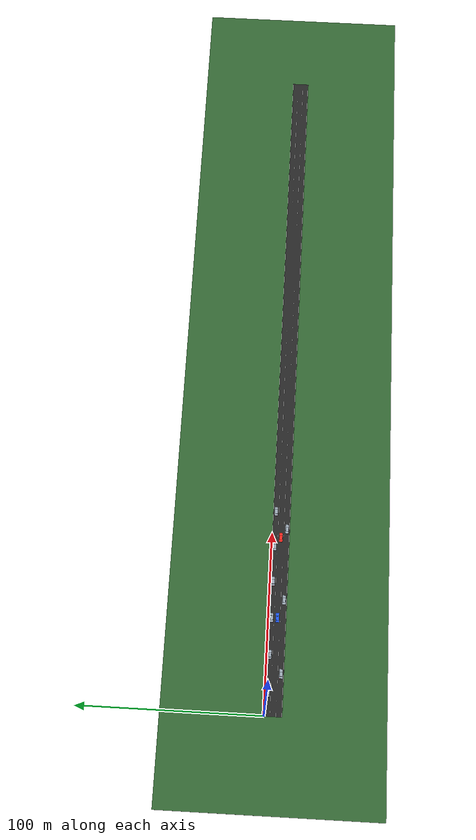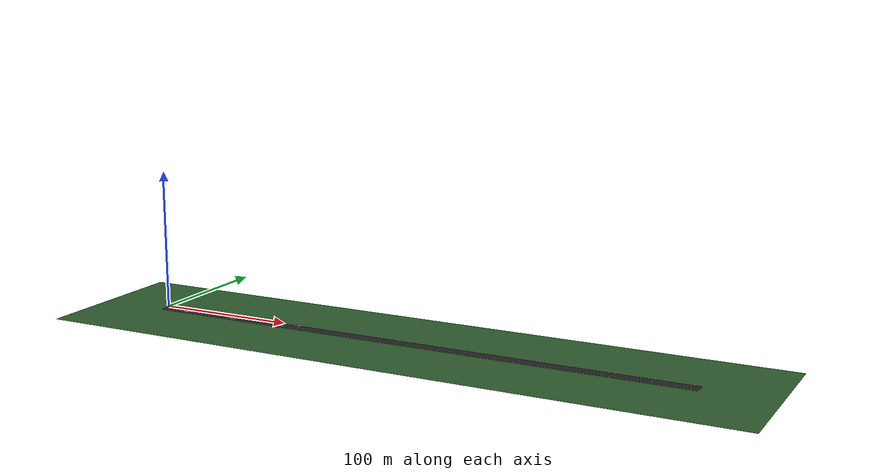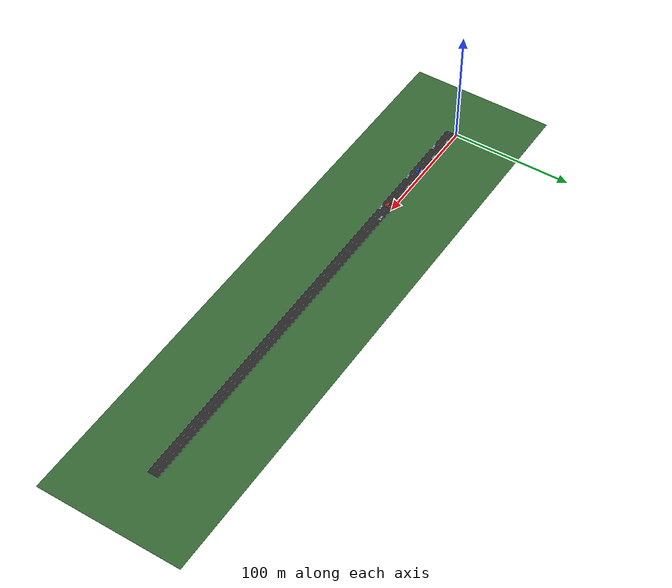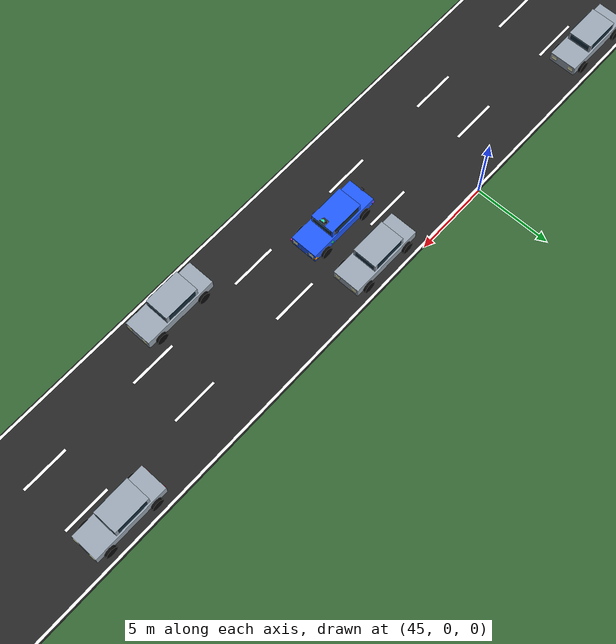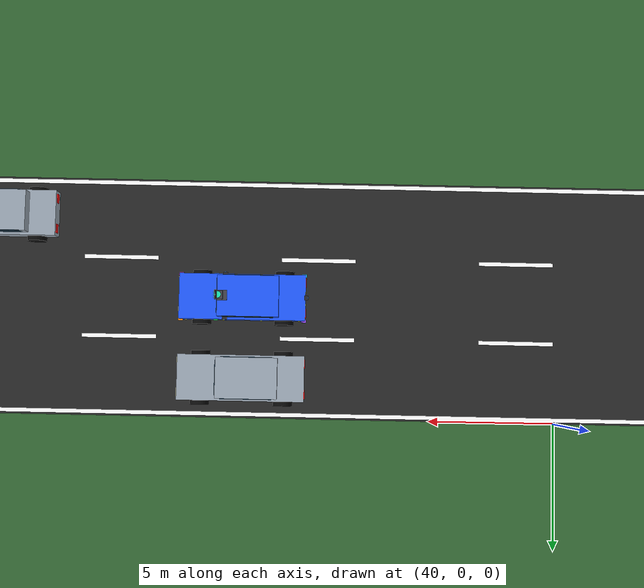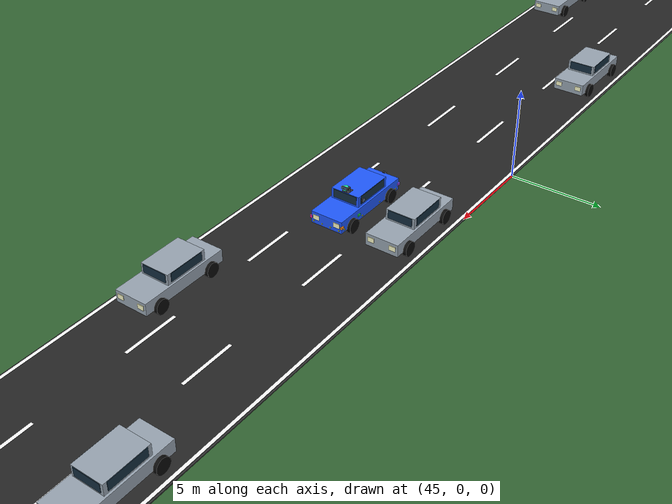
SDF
<?xml version='1.0' encoding='utf-8'?>
<sdf version="1.9">
  <world name="cosim_demo">
    <gravity>0 0 0</gravity>
    <physics name="default" type="ignored">
      <max_step_size>0.01</max_step_size>
      <real_time_factor>0</real_time_factor>
    </physics>
    <plugin filename="gz-sim-physics-system" name="gz::sim::systems::Physics" />
    <plugin filename="gz-sim-user-commands-system" name="gz::sim::systems::UserCommands" />
    <plugin filename="gz-sim-scene-broadcaster-system" name="gz::sim::systems::SceneBroadcaster" />
    <plugin filename="libcosim_sensor_render_sync.so" name="SensorRenderSync" />
    <plugin filename="gz-sim-sensors-system" name="gz::sim::systems::Sensors">
      <render_engine>ogre2</render_engine>
    </plugin>
    <light name="sun" type="directional">
      <pose>0 0 20 0 0 0</pose>
      <diffuse>0.9 0.9 0.9 1</diffuse>
      <direction>-0.3 -0.4 -1</direction>
    </light>
    <model name="road">
      <static>true</static>
      <link name="visuals">
        <visual name="grass">
          <pose>200.0 -4.8 -0.2 0 0 0</pose>
          <geometry>
            <box>
              <size>500 120 0.2</size>
            </box>
          </geometry>
          <material>
            <ambient>0.2 0.4 0.2 1</ambient>
            <diffuse>0.2 0.4 0.2 1</diffuse>
          </material>
        </visual>
        <visual name="asphalt">
          <pose>200.0 -4.8 -0.05 0 0 0</pose>
          <geometry>
            <box>
              <size>400 9.6 0.1</size>
            </box>
          </geometry>
          <material>
            <ambient>0.15 0.15 0.15 1</ambient>
            <diffuse>0.15 0.15 0.15 1</diffuse>
          </material>
        </visual>
        <visual name="edge_-0.15">
          <pose>200.0 -0.15 0.01 0 0 0</pose>
          <geometry>
            <box>
              <size>400 0.16 0.02</size>
            </box>
          </geometry>
          <material>
            <ambient>1 1 1 1</ambient>
            <diffuse>1 1 1 1</diffuse>
          </material>
        </visual>
        <visual name="edge_-9.45">
          <pose>200.0 -9.45 0.01 0 0 0</pose>
          <geometry>
            <box>
              <size>400 0.16 0.02</size>
            </box>
          </geometry>
          <material>
            <ambient>1 1 1 1</ambient>
            <diffuse>1 1 1 1</diffuse>
          </material>
        </visual>
        <visual name="dash_-3.2_0">
          <pose>1.5 -3.2 0.01 0 0 0</pose>
          <geometry>
            <box>
              <size>3 0.16 0.02</size>
            </box>
          </geometry>
          <material>
            <ambient>1 1 1 1</ambient>
            <diffuse>1 1 1 1</diffuse>
          </material>
        </visual>
        <visual name="dash_-3.2_8">
          <pose>9.5 -3.2 0.01 0 0 0</pose>
          <geometry>
            <box>
              <size>3 0.16 0.02</size>
            </box>
          </geometry>
          <material>
            <ambient>1 1 1 1</ambient>
            <diffuse>1 1 1 1</diffuse>
          </material>
        </visual>
        <visual name="dash_-3.2_16">
          <pose>17.5 -3.2 0.01 0 0 0</pose>
          <geometry>
            <box>
              <size>3 0.16 0.02</size>
            </box>
          </geometry>
          <material>
            <ambient>1 1 1 1</ambient>
            <diffuse>1 1 1 1</diffuse>
          </material>
        </visual>
        <visual name="dash_-3.2_24">
          <pose>25.5 -3.2 0.01 0 0 0</pose>
          <geometry>
            <box>
              <size>3 0.16 0.02</size>
            </box>
          </geometry>
          <material>
            <ambient>1 1 1 1</ambient>
            <diffuse>1 1 1 1</diffuse>
          </material>
        </visual>
        <visual name="dash_-3.2_32">
          <pose>33.5 -3.2 0.01 0 0 0</pose>
          <geometry>
            <box>
              <size>3 0.16 0.02</size>
            </box>
          </geometry>
          <material>
            <ambient>1 1 1 1</ambient>
            <diffuse>1 1 1 1</diffuse>
          </material>
        </visual>
        <visual name="dash_-3.2_40">
          <pose>41.5 -3.2 0.01 0 0 0</pose>
          <geometry>
            <box>
              <size>3 0.16 0.02</size>
            </box>
          </geometry>
          <material>
            <ambient>1 1 1 1</ambient>
            <diffuse>1 1 1 1</diffuse>
          </material>
        </visual>
        <visual name="dash_-3.2_48">
          <pose>49.5 -3.2 0.01 0 0 0</pose>
          <geometry>
            <box>
              <size>3 0.16 0.02</size>
            </box>
          </geometry>
          <material>
            <ambient>1 1 1 1</ambient>
            <diffuse>1 1 1 1</diffuse>
          </material>
        </visual>
        <visual name="dash_-3.2_56">
          <pose>57.5 -3.2 0.01 0 0 0</pose>
          <geometry>
            <box>
              <size>3 0.16 0.02</size>
            </box>
          </geometry>
          <material>
            <ambient>1 1 1 1</ambient>
            <diffuse>1 1 1 1</diffuse>
          </material>
        </visual>
        <visual name="dash_-3.2_64">
          <pose>65.5 -3.2 0.01 0 0 0</pose>
          <geometry>
            <box>
              <size>3 0.16 0.02</size>
            </box>
          </geometry>
          <material>
            <ambient>1 1 1 1</ambient>
            <diffuse>1 1 1 1</diffuse>
          </material>
        </visual>
        <visual name="dash_-3.2_72">
          <pose>73.5 -3.2 0.01 0 0 0</pose>
          <geometry>
            <box>
              <size>3 0.16 0.02</size>
            </box>
          </geometry>
          <material>
            <ambient>1 1 1 1</ambient>
            <diffuse>1 1 1 1</diffuse>
          </material>
        </visual>
        <visual name="dash_-3.2_80">
          <pose>81.5 -3.2 0.01 0 0 0</pose>
          <geometry>
            <box>
              <size>3 0.16 0.02</size>
            </box>
          </geometry>
          <material>
            <ambient>1 1 1 1</ambient>
            <diffuse>1 1 1 1</diffuse>
          </material>
        </visual>
        <visual name="dash_-3.2_88">
          <pose>89.5 -3.2 0.01 0 0 0</pose>
          <geometry>
            <box>
              <size>3 0.16 0.02</size>
            </box>
          </geometry>
          <material>
            <ambient>1 1 1 1</ambient>
            <diffuse>1 1 1 1</diffuse>
          </material>
        </visual>
        <visual name="dash_-3.2_96">
          <pose>97.5 -3.2 0.01 0 0 0</pose>
          <geometry>
            <box>
              <size>3 0.16 0.02</size>
            </box>
          </geometry>
          <material>
            <ambient>1 1 1 1</ambient>
            <diffuse>1 1 1 1</diffuse>
          </material>
        </visual>
        <visual name="dash_-3.2_104">
          <pose>105.5 -3.2 0.01 0 0 0</pose>
          <geometry>
            <box>
              <size>3 0.16 0.02</size>
            </box>
          </geometry>
          <material>
            <ambient>1 1 1 1</ambient>
            <diffuse>1 1 1 1</diffuse>
          </material>
        </visual>
        <visual name="dash_-3.2_112">
          <pose>113.5 -3.2 0.01 0 0 0</pose>
          <geometry>
            <box>
              <size>3 0.16 0.02</size>
            </box>
          </geometry>
          <material>
            <ambient>1 1 1 1</ambient>
            <diffuse>1 1 1 1</diffuse>
          </material>
        </visual>
        <visual name="dash_-3.2_120">
          <pose>121.5 -3.2 0.01 0 0 0</pose>
          <geometry>
            <box>
              <size>3 0.16 0.02</size>
            </box>
          </geometry>
          <material>
            <ambient>1 1 1 1</ambient>
            <diffuse>1 1 1 1</diffuse>
          </material>
        </visual>
        <visual name="dash_-3.2_128">
          <pose>129.5 -3.2 0.01 0 0 0</pose>
          <geometry>
            <box>
              <size>3 0.16 0.02</size>
            </box>
          </geometry>
          <material>
            <ambient>1 1 1 1</ambient>
            <diffuse>1 1 1 1</diffuse>
          </material>
        </visual>
        <visual name="dash_-3.2_136">
          <pose>137.5 -3.2 0.01 0 0 0</pose>
          <geometry>
            <box>
              <size>3 0.16 0.02</size>
            </box>
          </geometry>
          <material>
            <ambient>1 1 1 1</ambient>
            <diffuse>1 1 1 1</diffuse>
          </material>
        </visual>
        <visual name="dash_-3.2_144">
          <pose>145.5 -3.2 0.01 0 0 0</pose>
          <geometry>
            <box>
              <size>3 0.16 0.02</size>
            </box>
          </geometry>
          <material>
            <ambient>1 1 1 1</ambient>
            <diffuse>1 1 1 1</diffuse>
          </material>
        </visual>
        <visual name="dash_-3.2_152">
          <pose>153.5 -3.2 0.01 0 0 0</pose>
          <geometry>
            <box>
              <size>3 0.16 0.02</size>
            </box>
          </geometry>
          <material>
            <ambient>1 1 1 1</ambient>
            <diffuse>1 1 1 1</diffuse>
          </material>
        </visual>
        <visual name="dash_-3.2_160">
          <pose>161.5 -3.2 0.01 0 0 0</pose>
          <geometry>
            <box>
              <size>3 0.16 0.02</size>
            </box>
          </geometry>
          <material>
            <ambient>1 1 1 1</ambient>
            <diffuse>1 1 1 1</diffuse>
          </material>
        </visual>
        <visual name="dash_-3.2_168">
          <pose>169.5 -3.2 0.01 0 0 0</pose>
          <geometry>
            <box>
              <size>3 0.16 0.02</size>
            </box>
          </geometry>
          <material>
            <ambient>1 1 1 1</ambient>
            <diffuse>1 1 1 1</diffuse>
          </material>
        </visual>
        <visual name="dash_-3.2_176">
          <pose>177.5 -3.2 0.01 0 0 0</pose>
          <geometry>
            <box>
              <size>3 0.16 0.02</size>
            </box>
          </geometry>
          <material>
            <ambient>1 1 1 1</ambient>
            <diffuse>1 1 1 1</diffuse>
          </material>
        </visual>
        <visual name="dash_-3.2_184">
          <pose>185.5 -3.2 0.01 0 0 0</pose>
          <geometry>
            <box>
              <size>3 0.16 0.02</size>
            </box>
          </geometry>
          <material>
            <ambient>1 1 1 1</ambient>
            <diffuse>1 1 1 1</diffuse>
          </material>
        </visual>
        <visual name="dash_-3.2_192">
          <pose>193.5 -3.2 0.01 0 0 0</pose>
          <geometry>
            <box>
              <size>3 0.16 0.02</size>
            </box>
          </geometry>
          <material>
            <ambient>1 1 1 1</ambient>
            <diffuse>1 1 1 1</diffuse>
          </material>
        </visual>
        <visual name="dash_-3.2_200">
          <pose>201.5 -3.2 0.01 0 0 0</pose>
          <geometry>
            <box>
              <size>3 0.16 0.02</size>
            </box>
          </geometry>
          <material>
            <ambient>1 1 1 1</ambient>
            <diffuse>1 1 1 1</diffuse>
          </material>
        </visual>
        <visual name="dash_-3.2_208">
          <pose>209.5 -3.2 0.01 0 0 0</pose>
          <geometry>
            <box>
              <size>3 0.16 0.02</size>
            </box>
          </geometry>
          <material>
            <ambient>1 1 1 1</ambient>
            <diffuse>1 1 1 1</diffuse>
          </material>
        </visual>
        <visual name="dash_-3.2_216">
          <pose>217.5 -3.2 0.01 0 0 0</pose>
          <geometry>
            <box>
              <size>3 0.16 0.02</size>
            </box>
          </geometry>
          <material>
            <ambient>1 1 1 1</ambient>
            <diffuse>1 1 1 1</diffuse>
          </material>
        </visual>
        <visual name="dash_-3.2_224">
          <pose>225.5 -3.2 0.01 0 0 0</pose>
          <geometry>
            <box>
              <size>3 0.16 0.02</size>
            </box>
          </geometry>
          <material>
            <ambient>1 1 1 1</ambient>
            <diffuse>1 1 1 1</diffuse>
          </material>
        </visual>
        <visual name="dash_-3.2_232">
          <pose>233.5 -3.2 0.01 0 0 0</pose>
          <geometry>
            <box>
              <size>3 0.16 0.02</size>
            </box>
          </geometry>
          <material>
            <ambient>1 1 1 1</ambient>
            <diffuse>1 1 1 1</diffuse>
          </material>
        </visual>
        <visual name="dash_-3.2_240">
          <pose>241.5 -3.2 0.01 0 0 0</pose>
          <geometry>
            <box>
              <size>3 0.16 0.02</size>
            </box>
          </geometry>
          <material>
            <ambient>1 1 1 1</ambient>
            <diffuse>1 1 1 1</diffuse>
          </material>
        </visual>
        <visual name="dash_-3.2_248">
          <pose>249.5 -3.2 0.01 0 0 0</pose>
          <geometry>
            <box>
              <size>3 0.16 0.02</size>
            </box>
          </geometry>
          <material>
            <ambient>1 1 1 1</ambient>
            <diffuse>1 1 1 1</diffuse>
          </material>
        </visual>
        <visual name="dash_-3.2_256">
          <pose>257.5 -3.2 0.01 0 0 0</pose>
          <geometry>
            <box>
              <size>3 0.16 0.02</size>
            </box>
          </geometry>
          <material>
            <ambient>1 1 1 1</ambient>
            <diffuse>1 1 1 1</diffuse>
          </material>
        </visual>
        <visual name="dash_-3.2_264">
          <pose>265.5 -3.2 0.01 0 0 0</pose>
          <geometry>
            <box>
              <size>3 0.16 0.02</size>
            </box>
          </geometry>
          <material>
            <ambient>1 1 1 1</ambient>
            <diffuse>1 1 1 1</diffuse>
          </material>
        </visual>
        <visual name="dash_-3.2_272">
          <pose>273.5 -3.2 0.01 0 0 0</pose>
          <geometry>
            <box>
              <size>3 0.16 0.02</size>
            </box>
          </geometry>
          <material>
            <ambient>1 1 1 1</ambient>
            <diffuse>1 1 1 1</diffuse>
          </material>
        </visual>
        <visual name="dash_-3.2_280">
          <pose>281.5 -3.2 0.01 0 0 0</pose>
          <geometry>
            <box>
              <size>3 0.16 0.02</size>
            </box>
          </geometry>
          <material>
            <ambient>1 1 1 1</ambient>
            <diffuse>1 1 1 1</diffuse>
          </material>
        </visual>
        <visual name="dash_-3.2_288">
          <pose>289.5 -3.2 0.01 0 0 0</pose>
          <geometry>
            <box>
              <size>3 0.16 0.02</size>
            </box>
          </geometry>
          <material>
            <ambient>1 1 1 1</ambient>
            <diffuse>1 1 1 1</diffuse>
          </material>
        </visual>
        <visual name="dash_-3.2_296">
          <pose>297.5 -3.2 0.01 0 0 0</pose>
          <geometry>
            <box>
              <size>3 0.16 0.02</size>
            </box>
          </geometry>
          <material>
            <ambient>1 1 1 1</ambient>
            <diffuse>1 1 1 1</diffuse>
          </material>
        </visual>
        <visual name="dash_-3.2_304">
          <pose>305.5 -3.2 0.01 0 0 0</pose>
          <geometry>
            <box>
              <size>3 0.16 0.02</size>
            </box>
          </geometry>
          <material>
            <ambient>1 1 1 1</ambient>
            <diffuse>1 1 1 1</diffuse>
          </material>
        </visual>
        <visual name="dash_-3.2_312">
          <pose>313.5 -3.2 0.01 0 0 0</pose>
          <geometry>
            <box>
              <size>3 0.16 0.02</size>
            </box>
          </geometry>
          <material>
            <ambient>1 1 1 1</ambient>
            <diffuse>1 1 1 1</diffuse>
          </material>
        </visual>
        <visual name="dash_-3.2_320">
          <pose>321.5 -3.2 0.01 0 0 0</pose>
          <geometry>
            <box>
              <size>3 0.16 0.02</size>
            </box>
          </geometry>
          <material>
            <ambient>1 1 1 1</ambient>
            <diffuse>1 1 1 1</diffuse>
          </material>
        </visual>
        <visual name="dash_-3.2_328">
          <pose>329.5 -3.2 0.01 0 0 0</pose>
          <geometry>
            <box>
              <size>3 0.16 0.02</size>
            </box>
          </geometry>
          <material>
            <ambient>1 1 1 1</ambient>
            <diffuse>1 1 1 1</diffuse>
          </material>
        </visual>
        <visual name="dash_-3.2_336">
          <pose>337.5 -3.2 0.01 0 0 0</pose>
          <geometry>
            <box>
              <size>3 0.16 0.02</size>
            </box>
          </geometry>
          <material>
            <ambient>1 1 1 1</ambient>
            <diffuse>1 1 1 1</diffuse>
          </material>
        </visual>
        <visual name="dash_-3.2_344">
          <pose>345.5 -3.2 0.01 0 0 0</pose>
          <geometry>
            <box>
              <size>3 0.16 0.02</size>
            </box>
          </geometry>
          <material>
            <ambient>1 1 1 1</ambient>
            <diffuse>1 1 1 1</diffuse>
          </material>
        </visual>
        <visual name="dash_-3.2_352">
          <pose>353.5 -3.2 0.01 0 0 0</pose>
          <geometry>
            <box>
              <size>3 0.16 0.02</size>
            </box>
          </geometry>
          <material>
            <ambient>1 1 1 1</ambient>
            <diffuse>1 1 1 1</diffuse>
          </material>
        </visual>
        <visual name="dash_-3.2_360">
          <pose>361.5 -3.2 0.01 0 0 0</pose>
          <geometry>
            <box>
              <size>3 0.16 0.02</size>
            </box>
          </geometry>
          <material>
            <ambient>1 1 1 1</ambient>
            <diffuse>1 1 1 1</diffuse>
          </material>
        </visual>
        <visual name="dash_-3.2_368">
          <pose>369.5 -3.2 0.01 0 0 0</pose>
          <geometry>
            <box>
              <size>3 0.16 0.02</size>
            </box>
          </geometry>
          <material>
            <ambient>1 1 1 1</ambient>
            <diffuse>1 1 1 1</diffuse>
          </material>
        </visual>
        <visual name="dash_-3.2_376">
          <pose>377.5 -3.2 0.01 0 0 0</pose>
          <geometry>
            <box>
              <size>3 0.16 0.02</size>
            </box>
          </geometry>
          <material>
            <ambient>1 1 1 1</ambient>
            <diffuse>1 1 1 1</diffuse>
          </material>
        </visual>
        <visual name="dash_-3.2_384">
          <pose>385.5 -3.2 0.01 0 0 0</pose>
          <geometry>
            <box>
              <size>3 0.16 0.02</size>
            </box>
          </geometry>
          <material>
            <ambient>1 1 1 1</ambient>
            <diffuse>1 1 1 1</diffuse>
          </material>
        </visual>
        <visual name="dash_-3.2_392">
          <pose>393.5 -3.2 0.01 0 0 0</pose>
          <geometry>
            <box>
              <size>3 0.16 0.02</size>
            </box>
          </geometry>
          <material>
            <ambient>1 1 1 1</ambient>
            <diffuse>1 1 1 1</diffuse>
          </material>
        </visual>
        <visual name="dash_-6.4_0">
          <pose>1.5 -6.4 0.01 0 0 0</pose>
          <geometry>
            <box>
              <size>3 0.16 0.02</size>
            </box>
          </geometry>
          <material>
            <ambient>1 1 1 1</ambient>
            <diffuse>1 1 1 1</diffuse>
          </material>
        </visual>
        <visual name="dash_-6.4_8">
          <pose>9.5 -6.4 0.01 0 0 0</pose>
          <geometry>
            <box>
              <size>3 0.16 0.02</size>
            </box>
          </geometry>
          <material>
            <ambient>1 1 1 1</ambient>
            <diffuse>1 1 1 1</diffuse>
          </material>
        </visual>
        <visual name="dash_-6.4_16">
          <pose>17.5 -6.4 0.01 0 0 0</pose>
          <geometry>
            <box>
              <size>3 0.16 0.02</size>
            </box>
          </geometry>
          <material>
            <ambient>1 1 1 1</ambient>
            <diffuse>1 1 1 1</diffuse>
          </material>
        </visual>
        <visual name="dash_-6.4_24">
          <pose>25.5 -6.4 0.01 0 0 0</pose>
          <geometry>
            <box>
              <size>3 0.16 0.02</size>
            </box>
          </geometry>
          <material>
            <ambient>1 1 1 1</ambient>
            <diffuse>1 1 1 1</diffuse>
          </material>
        </visual>
        <visual name="dash_-6.4_32">
          <pose>33.5 -6.4 0.01 0 0 0</pose>
          <geometry>
            <box>
              <size>3 0.16 0.02</size>
            </box>
          </geometry>
          <material>
            <ambient>1 1 1 1</ambient>
            <diffuse>1 1 1 1</diffuse>
          </material>
        </visual>
        <visual name="dash_-6.4_40">
          <pose>41.5 -6.4 0.01 0 0 0</pose>
          <geometry>
            <box>
              <size>3 0.16 0.02</size>
            </box>
          </geometry>
          <material>
            <ambient>1 1 1 1</ambient>
            <diffuse>1 1 1 1</diffuse>
          </material>
        </visual>
        <visual name="dash_-6.4_48">
          <pose>49.5 -6.4 0.01 0 0 0</pose>
          <geometry>
            <box>
              <size>3 0.16 0.02</size>
            </box>
          </geometry>
          <material>
            <ambient>1 1 1 1</ambient>
            <diffuse>1 1 1 1</diffuse>
          </material>
        </visual>
        <visual name="dash_-6.4_56">
          <pose>57.5 -6.4 0.01 0 0 0</pose>
          <geometry>
            <box>
              <size>3 0.16 0.02</size>
            </box>
          </geometry>
          <material>
            <ambient>1 1 1 1</ambient>
            <diffuse>1 1 1 1</diffuse>
          </material>
        </visual>
        <visual name="dash_-6.4_64">
          <pose>65.5 -6.4 0.01 0 0 0</pose>
          <geometry>
            <box>
              <size>3 0.16 0.02</size>
            </box>
          </geometry>
          <material>
            <ambient>1 1 1 1</ambient>
            <diffuse>1 1 1 1</diffuse>
          </material>
        </visual>
        <visual name="dash_-6.4_72">
          <pose>73.5 -6.4 0.01 0 0 0</pose>
          <geometry>
            <box>
              <size>3 0.16 0.02</size>
            </box>
          </geometry>
          <material>
            <ambient>1 1 1 1</ambient>
            <diffuse>1 1 1 1</diffuse>
          </material>
        </visual>
        <visual name="dash_-6.4_80">
          <pose>81.5 -6.4 0.01 0 0 0</pose>
          <geometry>
            <box>
              <size>3 0.16 0.02</size>
            </box>
          </geometry>
          <material>
            <ambient>1 1 1 1</ambient>
            <diffuse>1 1 1 1</diffuse>
          </material>
        </visual>
        <visual name="dash_-6.4_88">
          <pose>89.5 -6.4 0.01 0 0 0</pose>
          <geometry>
            <box>
              <size>3 0.16 0.02</size>
            </box>
          </geometry>
          <material>
            <ambient>1 1 1 1</ambient>
            <diffuse>1 1 1 1</diffuse>
          </material>
        </visual>
        <visual name="dash_-6.4_96">
          <pose>97.5 -6.4 0.01 0 0 0</pose>
          <geometry>
            <box>
              <size>3 0.16 0.02</size>
            </box>
          </geometry>
          <material>
            <ambient>1 1 1 1</ambient>
            <diffuse>1 1 1 1</diffuse>
          </material>
        </visual>
        <visual name="dash_-6.4_104">
          <pose>105.5 -6.4 0.01 0 0 0</pose>
          <geometry>
            <box>
              <size>3 0.16 0.02</size>
            </box>
          </geometry>
          <material>
            <ambient>1 1 1 1</ambient>
            <diffuse>1 1 1 1</diffuse>
          </material>
        </visual>
        <visual name="dash_-6.4_112">
          <pose>113.5 -6.4 0.01 0 0 0</pose>
          <geometry>
            <box>
              <size>3 0.16 0.02</size>
            </box>
          </geometry>
          <material>
            <ambient>1 1 1 1</ambient>
            <diffuse>1 1 1 1</diffuse>
          </material>
        </visual>
        <visual name="dash_-6.4_120">
          <pose>121.5 -6.4 0.01 0 0 0</pose>
          <geometry>
            <box>
              <size>3 0.16 0.02</size>
            </box>
          </geometry>
          <material>
            <ambient>1 1 1 1</ambient>
            <diffuse>1 1 1 1</diffuse>
          </material>
        </visual>
        <visual name="dash_-6.4_128">
          <pose>129.5 -6.4 0.01 0 0 0</pose>
          <geometry>
            <box>
              <size>3 0.16 0.02</size>
            </box>
          </geometry>
          <material>
            <ambient>1 1 1 1</ambient>
            <diffuse>1 1 1 1</diffuse>
          </material>
        </visual>
        <visual name="dash_-6.4_136">
          <pose>137.5 -6.4 0.01 0 0 0</pose>
          <geometry>
            <box>
              <size>3 0.16 0.02</size>
            </box>
          </geometry>
          <material>
            <ambient>1 1 1 1</ambient>
            <diffuse>1 1 1 1</diffuse>
          </material>
        </visual>
        <visual name="dash_-6.4_144">
          <pose>145.5 -6.4 0.01 0 0 0</pose>
          <geometry>
            <box>
              <size>3 0.16 0.02</size>
            </box>
          </geometry>
          <material>
            <ambient>1 1 1 1</ambient>
            <diffuse>1 1 1 1</diffuse>
          </material>
        </visual>
        <visual name="dash_-6.4_152">
          <pose>153.5 -6.4 0.01 0 0 0</pose>
          <geometry>
            <box>
              <size>3 0.16 0.02</size>
            </box>
          </geometry>
          <material>
            <ambient>1 1 1 1</ambient>
            <diffuse>1 1 1 1</diffuse>
          </material>
        </visual>
        <visual name="dash_-6.4_160">
          <pose>161.5 -6.4 0.01 0 0 0</pose>
          <geometry>
            <box>
              <size>3 0.16 0.02</size>
            </box>
          </geometry>
          <material>
            <ambient>1 1 1 1</ambient>
            <diffuse>1 1 1 1</diffuse>
          </material>
        </visual>
        <visual name="dash_-6.4_168">
          <pose>169.5 -6.4 0.01 0 0 0</pose>
          <geometry>
            <box>
              <size>3 0.16 0.02</size>
            </box>
          </geometry>
          <material>
            <ambient>1 1 1 1</ambient>
            <diffuse>1 1 1 1</diffuse>
          </material>
        </visual>
        <visual name="dash_-6.4_176">
          <pose>177.5 -6.4 0.01 0 0 0</pose>
          <geometry>
            <box>
              <size>3 0.16 0.02</size>
            </box>
          </geometry>
          <material>
            <ambient>1 1 1 1</ambient>
            <diffuse>1 1 1 1</diffuse>
          </material>
        </visual>
        <visual name="dash_-6.4_184">
          <pose>185.5 -6.4 0.01 0 0 0</pose>
          <geometry>
            <box>
              <size>3 0.16 0.02</size>
            </box>
          </geometry>
          <material>
            <ambient>1 1 1 1</ambient>
            <diffuse>1 1 1 1</diffuse>
          </material>
        </visual>
        <visual name="dash_-6.4_192">
          <pose>193.5 -6.4 0.01 0 0 0</pose>
          <geometry>
            <box>
              <size>3 0.16 0.02</size>
            </box>
          </geometry>
          <material>
            <ambient>1 1 1 1</ambient>
            <diffuse>1 1 1 1</diffuse>
          </material>
        </visual>
        <visual name="dash_-6.4_200">
          <pose>201.5 -6.4 0.01 0 0 0</pose>
          <geometry>
            <box>
              <size>3 0.16 0.02</size>
            </box>
          </geometry>
          <material>
            <ambient>1 1 1 1</ambient>
            <diffuse>1 1 1 1</diffuse>
          </material>
        </visual>
        <visual name="dash_-6.4_208">
          <pose>209.5 -6.4 0.01 0 0 0</pose>
          <geometry>
            <box>
              <size>3 0.16 0.02</size>
            </box>
          </geometry>
          <material>
            <ambient>1 1 1 1</ambient>
            <diffuse>1 1 1 1</diffuse>
          </material>
        </visual>
        <visual name="dash_-6.4_216">
          <pose>217.5 -6.4 0.01 0 0 0</pose>
          <geometry>
            <box>
              <size>3 0.16 0.02</size>
            </box>
          </geometry>
          <material>
            <ambient>1 1 1 1</ambient>
            <diffuse>1 1 1 1</diffuse>
          </material>
        </visual>
        <visual name="dash_-6.4_224">
          <pose>225.5 -6.4 0.01 0 0 0</pose>
          <geometry>
            <box>
              <size>3 0.16 0.02</size>
            </box>
          </geometry>
          <material>
            <ambient>1 1 1 1</ambient>
            <diffuse>1 1 1 1</diffuse>
          </material>
        </visual>
        <visual name="dash_-6.4_232">
          <pose>233.5 -6.4 0.01 0 0 0</pose>
          <geometry>
            <box>
              <size>3 0.16 0.02</size>
            </box>
          </geometry>
          <material>
            <ambient>1 1 1 1</ambient>
            <diffuse>1 1 1 1</diffuse>
          </material>
        </visual>
        <visual name="dash_-6.4_240">
          <pose>241.5 -6.4 0.01 0 0 0</pose>
          <geometry>
            <box>
              <size>3 0.16 0.02</size>
            </box>
          </geometry>
          <material>
            <ambient>1 1 1 1</ambient>
            <diffuse>1 1 1 1</diffuse>
          </material>
        </visual>
        <visual name="dash_-6.4_248">
          <pose>249.5 -6.4 0.01 0 0 0</pose>
          <geometry>
            <box>
              <size>3 0.16 0.02</size>
            </box>
          </geometry>
          <material>
            <ambient>1 1 1 1</ambient>
            <diffuse>1 1 1 1</diffuse>
          </material>
        </visual>
        <visual name="dash_-6.4_256">
          <pose>257.5 -6.4 0.01 0 0 0</pose>
          <geometry>
            <box>
              <size>3 0.16 0.02</size>
            </box>
          </geometry>
          <material>
            <ambient>1 1 1 1</ambient>
            <diffuse>1 1 1 1</diffuse>
          </material>
        </visual>
        <visual name="dash_-6.4_264">
          <pose>265.5 -6.4 0.01 0 0 0</pose>
          <geometry>
            <box>
              <size>3 0.16 0.02</size>
            </box>
          </geometry>
          <material>
            <ambient>1 1 1 1</ambient>
            <diffuse>1 1 1 1</diffuse>
          </material>
        </visual>
        <visual name="dash_-6.4_272">
          <pose>273.5 -6.4 0.01 0 0 0</pose>
          <geometry>
            <box>
              <size>3 0.16 0.02</size>
            </box>
          </geometry>
          <material>
            <ambient>1 1 1 1</ambient>
            <diffuse>1 1 1 1</diffuse>
          </material>
        </visual>
        <visual name="dash_-6.4_280">
          <pose>281.5 -6.4 0.01 0 0 0</pose>
          <geometry>
            <box>
              <size>3 0.16 0.02</size>
            </box>
          </geometry>
          <material>
            <ambient>1 1 1 1</ambient>
            <diffuse>1 1 1 1</diffuse>
          </material>
        </visual>
        <visual name="dash_-6.4_288">
          <pose>289.5 -6.4 0.01 0 0 0</pose>
          <geometry>
            <box>
              <size>3 0.16 0.02</size>
            </box>
          </geometry>
          <material>
            <ambient>1 1 1 1</ambient>
            <diffuse>1 1 1 1</diffuse>
          </material>
        </visual>
        <visual name="dash_-6.4_296">
          <pose>297.5 -6.4 0.01 0 0 0</pose>
          <geometry>
            <box>
              <size>3 0.16 0.02</size>
            </box>
          </geometry>
          <material>
            <ambient>1 1 1 1</ambient>
            <diffuse>1 1 1 1</diffuse>
          </material>
        </visual>
        <visual name="dash_-6.4_304">
          <pose>305.5 -6.4 0.01 0 0 0</pose>
          <geometry>
            <box>
              <size>3 0.16 0.02</size>
            </box>
          </geometry>
          <material>
            <ambient>1 1 1 1</ambient>
            <diffuse>1 1 1 1</diffuse>
          </material>
        </visual>
        <visual name="dash_-6.4_312">
          <pose>313.5 -6.4 0.01 0 0 0</pose>
          <geometry>
            <box>
              <size>3 0.16 0.02</size>
            </box>
          </geometry>
          <material>
            <ambient>1 1 1 1</ambient>
            <diffuse>1 1 1 1</diffuse>
          </material>
        </visual>
        <visual name="dash_-6.4_320">
          <pose>321.5 -6.4 0.01 0 0 0</pose>
          <geometry>
            <box>
              <size>3 0.16 0.02</size>
            </box>
          </geometry>
          <material>
            <ambient>1 1 1 1</ambient>
            <diffuse>1 1 1 1</diffuse>
          </material>
        </visual>
        <visual name="dash_-6.4_328">
          <pose>329.5 -6.4 0.01 0 0 0</pose>
          <geometry>
            <box>
              <size>3 0.16 0.02</size>
            </box>
          </geometry>
          <material>
            <ambient>1 1 1 1</ambient>
            <diffuse>1 1 1 1</diffuse>
          </material>
        </visual>
        <visual name="dash_-6.4_336">
          <pose>337.5 -6.4 0.01 0 0 0</pose>
          <geometry>
            <box>
              <size>3 0.16 0.02</size>
            </box>
          </geometry>
          <material>
            <ambient>1 1 1 1</ambient>
            <diffuse>1 1 1 1</diffuse>
          </material>
        </visual>
        <visual name="dash_-6.4_344">
          <pose>345.5 -6.4 0.01 0 0 0</pose>
          <geometry>
            <box>
              <size>3 0.16 0.02</size>
            </box>
          </geometry>
          <material>
            <ambient>1 1 1 1</ambient>
            <diffuse>1 1 1 1</diffuse>
          </material>
        </visual>
        <visual name="dash_-6.4_352">
          <pose>353.5 -6.4 0.01 0 0 0</pose>
          <geometry>
            <box>
              <size>3 0.16 0.02</size>
            </box>
          </geometry>
          <material>
            <ambient>1 1 1 1</ambient>
            <diffuse>1 1 1 1</diffuse>
          </material>
        </visual>
        <visual name="dash_-6.4_360">
          <pose>361.5 -6.4 0.01 0 0 0</pose>
          <geometry>
            <box>
              <size>3 0.16 0.02</size>
            </box>
          </geometry>
          <material>
            <ambient>1 1 1 1</ambient>
            <diffuse>1 1 1 1</diffuse>
          </material>
        </visual>
        <visual name="dash_-6.4_368">
          <pose>369.5 -6.4 0.01 0 0 0</pose>
          <geometry>
            <box>
              <size>3 0.16 0.02</size>
            </box>
          </geometry>
          <material>
            <ambient>1 1 1 1</ambient>
            <diffuse>1 1 1 1</diffuse>
          </material>
        </visual>
        <visual name="dash_-6.4_376">
          <pose>377.5 -6.4 0.01 0 0 0</pose>
          <geometry>
            <box>
              <size>3 0.16 0.02</size>
            </box>
          </geometry>
          <material>
            <ambient>1 1 1 1</ambient>
            <diffuse>1 1 1 1</diffuse>
          </material>
        </visual>
        <visual name="dash_-6.4_384">
          <pose>385.5 -6.4 0.01 0 0 0</pose>
          <geometry>
            <box>
              <size>3 0.16 0.02</size>
            </box>
          </geometry>
          <material>
            <ambient>1 1 1 1</ambient>
            <diffuse>1 1 1 1</diffuse>
          </material>
        </visual>
        <visual name="dash_-6.4_392">
          <pose>393.5 -6.4 0.01 0 0 0</pose>
          <geometry>
            <box>
              <size>3 0.16 0.02</size>
            </box>
          </geometry>
          <material>
            <ambient>1 1 1 1</ambient>
            <diffuse>1 1 1 1</diffuse>
          </material>
        </visual>
      </link>
    </model>
    <include>
      <uri>model://car_a</uri>
      <name>car_a</name>
      <pose>97.5 -4.8 0 0 0 0</pose>
    </include>
    <include>
      <uri>model://car_b</uri>
      <name>car_b</name>
      <pose>52.5 -4.8 0 0 0 0</pose>
    </include>
    <include>
      <uri>model://background_car</uri>
      <name>bg_01</name>
      <pose>12.5 -1.5999999999999996 0 0 0 0</pose>
    </include>
    <include>
      <uri>model://background_car</uri>
      <name>bg_02</name>
      <pose>32.5 -1.5999999999999996 0 0 0 0</pose>
    </include>
    <include>
      <uri>model://background_car</uri>
      <name>bg_03</name>
      <pose>52.5 -1.5999999999999996 0 0 0 0</pose>
    </include>
    <include>
      <uri>model://background_car</uri>
      <name>bg_04</name>
      <pose>72.5 -1.5999999999999996 0 0 0 0</pose>
    </include>
    <include>
      <uri>model://background_car</uri>
      <name>bg_05</name>
      <pose>92.5 -1.5999999999999996 0 0 0 0</pose>
    </include>
    <include>
      <uri>model://background_car</uri>
      <name>bg_06</name>
      <pose>112.5 -1.5999999999999996 0 0 0 0</pose>
    </include>
    <include>
      <uri>model://background_car</uri>
      <name>bg_07</name>
      <pose>22.5 -8.0 0 0 0 0</pose>
    </include>
    <include>
      <uri>model://background_car</uri>
      <name>bg_08</name>
      <pose>62.5 -8.0 0 0 0 0</pose>
    </include>
    <include>
      <uri>model://background_car</uri>
      <name>bg_09</name>
      <pose>102.5 -8.0 0 0 0 0</pose>
    </include>
  </world>
</sdf>

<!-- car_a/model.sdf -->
<sdf version="1.9">
  <model name="car_a">
    <static>true</static>
    <link name="body">
      <visual name="chassis">
        <pose>0 0 0.65 0 0 0</pose>
        <geometry>
          <box>
            <size>5 1.8 0.65</size>
          </box>
        </geometry>
        <material>
          <ambient>1 0.15 0.12 1</ambient>
          <diffuse>1 0.15 0.12 1</diffuse>
        </material>
      </visual>
      <visual name="cabin">
        <pose>-0.25 0 1.2 0 0 0</pose>
        <geometry>
          <box>
            <size>2.4 1.6 0.7</size>
          </box>
        </geometry>
        <material>
          <ambient>1 0.15 0.12 1</ambient>
          <diffuse>1 0.15 0.12 1</diffuse>
        </material>
      </visual>
      <visual name="windshield">
        <pose>0.96 0 1.3 0 0 0</pose>
        <geometry>
          <box>
            <size>0.03 1.35 0.45</size>
          </box>
        </geometry>
        <material>
          <ambient>0.08 0.18 0.25 1</ambient>
          <diffuse>0.08 0.18 0.25 1</diffuse>
        </material>
      </visual>
      <visual name="window-1">
        <pose>-0.25 -0.81 1.3 0 0 0</pose>
        <geometry>
          <box>
            <size>2 0.03 0.45</size>
          </box>
        </geometry>
        <material>
          <ambient>0.08 0.18 0.25 1</ambient>
          <diffuse>0.08 0.18 0.25 1</diffuse>
        </material>
      </visual>
      <visual name="wheel-1.65_-1">
        <pose>-1.65 -0.95 0.38 1.570796 0 0</pose>
        <geometry>
          <cylinder>
            <radius>0.38</radius>
            <length>0.25</length>
          </cylinder>
        </geometry>
        <material>
          <ambient>0.04 0.04 0.04 1</ambient>
          <diffuse>0.04 0.04 0.04 1</diffuse>
        </material>
      </visual>
      <visual name="wheel1.65_-1">
        <pose>1.65 -0.95 0.38 1.570796 0 0</pose>
        <geometry>
          <cylinder>
            <radius>0.38</radius>
            <length>0.25</length>
          </cylinder>
        </geometry>
        <material>
          <ambient>0.04 0.04 0.04 1</ambient>
          <diffuse>0.04 0.04 0.04 1</diffuse>
        </material>
      </visual>
      <visual name="headlight-1">
        <pose>2.51 -0.6 0.7 0 0 0</pose>
        <geometry>
          <box>
            <size>0.04 0.35 0.25</size>
          </box>
        </geometry>
        <material>
          <ambient>1 1 0.8 1</ambient>
          <diffuse>1 1 0.8 1</diffuse>
        </material>
      </visual>
      <visual name="taillight-1">
        <pose>-2.51 -0.6 0.7 0 0 0</pose>
        <geometry>
          <box>
            <size>0.04 0.35 0.25</size>
          </box>
        </geometry>
        <material>
          <ambient>1 0.05 0.05 1</ambient>
          <diffuse>1 0.05 0.05 1</diffuse>
        </material>
      </visual>
      <visual name="window1">
        <pose>-0.25 0.81 1.3 0 0 0</pose>
        <geometry>
          <box>
            <size>2 0.03 0.45</size>
          </box>
        </geometry>
        <material>
          <ambient>0.08 0.18 0.25 1</ambient>
          <diffuse>0.08 0.18 0.25 1</diffuse>
        </material>
      </visual>
      <visual name="wheel-1.65_1">
        <pose>-1.65 0.95 0.38 1.570796 0 0</pose>
        <geometry>
          <cylinder>
            <radius>0.38</radius>
            <length>0.25</length>
          </cylinder>
        </geometry>
        <material>
          <ambient>0.04 0.04 0.04 1</ambient>
          <diffuse>0.04 0.04 0.04 1</diffuse>
        </material>
      </visual>
      <visual name="wheel1.65_1">
        <pose>1.65 0.95 0.38 1.570796 0 0</pose>
        <geometry>
          <cylinder>
            <radius>0.38</radius>
            <length>0.25</length>
          </cylinder>
        </geometry>
        <material>
          <ambient>0.04 0.04 0.04 1</ambient>
          <diffuse>0.04 0.04 0.04 1</diffuse>
        </material>
      </visual>
      <visual name="headlight1">
        <pose>2.51 0.6 0.7 0 0 0</pose>
        <geometry>
          <box>
            <size>0.04 0.35 0.25</size>
          </box>
        </geometry>
        <material>
          <ambient>1 1 0.8 1</ambient>
          <diffuse>1 1 0.8 1</diffuse>
        </material>
      </visual>
      <visual name="taillight1">
        <pose>-2.51 0.6 0.7 0 0 0</pose>
        <geometry>
          <box>
            <size>0.04 0.35 0.25</size>
          </box>
        </geometry>
        <material>
          <ambient>1 0.05 0.05 1</ambient>
          <diffuse>1 0.05 0.05 1</diffuse>
        </material>
      </visual>
    </link>
  </model>
</sdf>

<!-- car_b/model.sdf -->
<sdf version="1.9">
  <model name="car_b">
    <static>true</static>
    <include merge="true"><uri>model://perception_rig</uri></include>
    <include merge="true"><uri>model://corner_radar_rig</uri></include>
    <include merge="true"><uri>model://side_radar_rig</uri></include>
    <include merge="true"><uri>model://surround_camera_rig</uri></include>
    <include merge="true"><uri>model://ultrasonic_rig</uri></include>
    <link name="body">
      <visual name="chassis">
        <pose>0 0 0.65 0 0 0</pose>
        <geometry>
          <box>
            <size>5 1.8 0.65</size>
          </box>
        </geometry>
        <material>
          <ambient>0.12 0.35 1 1</ambient>
          <diffuse>0.12 0.35 1 1</diffuse>
        </material>
      </visual>
      <visual name="cabin">
        <pose>-0.25 0 1.2 0 0 0</pose>
        <geometry>
          <box>
            <size>2.4 1.6 0.7</size>
          </box>
        </geometry>
        <material>
          <ambient>0.12 0.35 1 1</ambient>
          <diffuse>0.12 0.35 1 1</diffuse>
        </material>
      </visual>
      <visual name="windshield">
        <pose>0.96 0 1.3 0 0 0</pose>
        <geometry>
          <box>
            <size>0.03 1.35 0.45</size>
          </box>
        </geometry>
        <material>
          <ambient>0.08 0.18 0.25 1</ambient>
          <diffuse>0.08 0.18 0.25 1</diffuse>
        </material>
      </visual>
      <visual name="window-1">
        <pose>-0.25 -0.81 1.3 0 0 0</pose>
        <geometry>
          <box>
            <size>2 0.03 0.45</size>
          </box>
        </geometry>
        <material>
          <ambient>0.08 0.18 0.25 1</ambient>
          <diffuse>0.08 0.18 0.25 1</diffuse>
        </material>
      </visual>
      <visual name="wheel-1.65_-1">
        <pose>-1.65 -0.95 0.38 1.570796 0 0</pose>
        <geometry>
          <cylinder>
            <radius>0.38</radius>
            <length>0.25</length>
          </cylinder>
        </geometry>
        <material>
          <ambient>0.04 0.04 0.04 1</ambient>
          <diffuse>0.04 0.04 0.04 1</diffuse>
        </material>
      </visual>
      <visual name="wheel1.65_-1">
        <pose>1.65 -0.95 0.38 1.570796 0 0</pose>
        <geometry>
          <cylinder>
            <radius>0.38</radius>
            <length>0.25</length>
          </cylinder>
        </geometry>
        <material>
          <ambient>0.04 0.04 0.04 1</ambient>
          <diffuse>0.04 0.04 0.04 1</diffuse>
        </material>
      </visual>
      <visual name="headlight-1">
        <pose>2.51 -0.6 0.7 0 0 0</pose>
        <geometry>
          <box>
            <size>0.04 0.35 0.25</size>
          </box>
        </geometry>
        <material>
          <ambient>1 1 0.8 1</ambient>
          <diffuse>1 1 0.8 1</diffuse>
        </material>
      </visual>
      <visual name="taillight-1">
        <pose>-2.51 -0.6 0.7 0 0 0</pose>
        <geometry>
          <box>
            <size>0.04 0.35 0.25</size>
          </box>
        </geometry>
        <material>
          <ambient>1 0.05 0.05 1</ambient>
          <diffuse>1 0.05 0.05 1</diffuse>
        </material>
      </visual>
      <visual name="window1">
        <pose>-0.25 0.81 1.3 0 0 0</pose>
        <geometry>
          <box>
            <size>2 0.03 0.45</size>
          </box>
        </geometry>
        <material>
          <ambient>0.08 0.18 0.25 1</ambient>
          <diffuse>0.08 0.18 0.25 1</diffuse>
        </material>
      </visual>
      <visual name="wheel-1.65_1">
        <pose>-1.65 0.95 0.38 1.570796 0 0</pose>
        <geometry>
          <cylinder>
            <radius>0.38</radius>
            <length>0.25</length>
          </cylinder>
        </geometry>
        <material>
          <ambient>0.04 0.04 0.04 1</ambient>
          <diffuse>0.04 0.04 0.04 1</diffuse>
        </material>
      </visual>
      <visual name="wheel1.65_1">
        <pose>1.65 0.95 0.38 1.570796 0 0</pose>
        <geometry>
          <cylinder>
            <radius>0.38</radius>
            <length>0.25</length>
          </cylinder>
        </geometry>
        <material>
          <ambient>0.04 0.04 0.04 1</ambient>
          <diffuse>0.04 0.04 0.04 1</diffuse>
        </material>
      </visual>
      <visual name="headlight1">
        <pose>2.51 0.6 0.7 0 0 0</pose>
        <geometry>
          <box>
            <size>0.04 0.35 0.25</size>
          </box>
        </geometry>
        <material>
          <ambient>1 1 0.8 1</ambient>
          <diffuse>1 1 0.8 1</diffuse>
        </material>
      </visual>
      <visual name="taillight1">
        <pose>-2.51 0.6 0.7 0 0 0</pose>
        <geometry>
          <box>
            <size>0.04 0.35 0.25</size>
          </box>
        </geometry>
        <material>
          <ambient>1 0.05 0.05 1</ambient>
          <diffuse>1 0.05 0.05 1</diffuse>
        </material>
      </visual>
    </link>
  </model>
</sdf>

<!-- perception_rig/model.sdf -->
<sdf version="1.9">
  <!-- 以车辆中心为原点，x 前、y 左、z 上；话题使用 Gazebo 自动模型作用域。 -->
  <model name="perception_rig">
    <static>true</static>
    <link name="sensor_mount">
      <!-- 车顶 z=1.55；底板、支柱与机身相接，不悬空。 -->
      <visual name="mounting_plate">
        <pose>0.75 0 1.57 0 0 0</pose>
        <geometry><box><size>0.38 0.40 0.04</size></box></geometry>
        <material><ambient>0.25 0.25 0.28 1</ambient><diffuse>0.25 0.25 0.28 1</diffuse></material>
      </visual>
      <visual name="lidar_pedestal">
        <pose>0.82 0 1.64 0 0 0</pose>
        <geometry><cylinder><radius>0.06</radius><length>0.18</length></cylinder></geometry>
        <material><ambient>0.25 0.25 0.28 1</ambient><diffuse>0.25 0.25 0.28 1</diffuse></material>
      </visual>
      <visual name="lidar_housing">
        <pose>0.90 0 1.78 0 0 0</pose>
        <geometry><cylinder><radius>0.13</radius><length>0.2</length></cylinder></geometry>
        <material><ambient>0.1 0.9 0.7 1</ambient><diffuse>0.1 0.9 0.7 1</diffuse></material>
      </visual>
      <visual name="camera_pedestal">
        <pose>0.74 0 1.67 0 0 0</pose>
        <geometry><box><size>0.06 0.32 0.24</size></box></geometry>
        <material><ambient>0.25 0.25 0.28 1</ambient><diffuse>0.25 0.25 0.28 1</diffuse></material>
      </visual>
      <visual name="camera_arm">
        <pose>0.86 0 1.79 0 0 0</pose>
        <geometry><box><size>0.30 0.32 0.04</size></box></geometry>
        <material><ambient>0.25 0.25 0.28 1</ambient><diffuse>0.25 0.25 0.28 1</diffuse></material>
      </visual>
      <visual name="camera_housing">
        <pose>0.98 0 1.82 0 0 0</pose>
        <geometry><box><size>0.1 0.36 0.12</size></box></geometry>
        <material><ambient>0.05 0.05 0.05 1</ambient><diffuse>0.05 0.05 0.05 1</diffuse></material>
      </visual>
      <visual name="wide_lens">
        <pose>1.04 0.10 1.85 0 0 0</pose>
        <geometry><box><size>0.04 0.055 0.055</size></box></geometry>
        <material><ambient>0.2 0.6 1 1</ambient><diffuse>0.2 0.6 1 1</diffuse></material>
      </visual>
      <visual name="standard_lens">
        <pose>1.04 0 1.85 0 0 0</pose>
        <geometry><box><size>0.04 0.055 0.055</size></box></geometry>
        <material><ambient>0.2 0.6 1 1</ambient><diffuse>0.2 0.6 1 1</diffuse></material>
      </visual>
      <visual name="tele_lens">
        <pose>1.04 -0.10 1.85 0 0 0</pose>
        <geometry><box><size>0.04 0.055 0.055</size></box></geometry>
        <material><ambient>0.2 0.6 1 1</ambient><diffuse>0.2 0.6 1 1</diffuse></material>
      </visual>
      <sensor name="lidar" type="gpu_lidar">
        <pose>0.90 0 1.85 0 0 0</pose>
        <always_on>true</always_on><update_rate>10</update_rate>
        <lidar>
          <scan>
            <horizontal><samples>720</samples><resolution>1</resolution><min_angle>-1.0471975512</min_angle><max_angle>1.0471975512</max_angle></horizontal>
            <vertical><samples>64</samples><resolution>1</resolution><min_angle>-0.4363323130</min_angle><max_angle>0.2617993878</max_angle></vertical>
          </scan>
          <range><min>0.3</min><max>100</max><resolution>0.01</resolution></range>
        </lidar>
      </sensor>
      <!-- 车顶前缘 x=0.95、顶面 z=1.55；镜头略向前伸且高于顶面。 -->
      <sensor name="wide" type="camera">
        <pose>1.05 0.10 1.85 0 0.1745329252 0</pose>
        <always_on>true</always_on><update_rate>15</update_rate>
        <camera><horizontal_fov>2.3561944902</horizontal_fov><image><width>640</width><height>360</height><format>R8G8B8</format></image><clip><near>0.05</near><far>150</far></clip></camera>
      </sensor>
      <sensor name="standard" type="camera">
        <pose>1.05 0 1.85 0 0.0872664626 0</pose>
        <always_on>true</always_on><update_rate>15</update_rate>
        <camera><horizontal_fov>1.0471975512</horizontal_fov><image><width>640</width><height>360</height><format>R8G8B8</format></image><clip><near>0.05</near><far>150</far></clip></camera>
      </sensor>
      <sensor name="tele" type="camera">
        <pose>1.05 -0.10 1.85 0 0 0</pose>
        <always_on>true</always_on><update_rate>15</update_rate>
        <camera><horizontal_fov>0.3490658504</horizontal_fov><image><width>640</width><height>360</height><format>R8G8B8</format></image><clip><near>0.05</near><far>300</far></clip></camera>
      </sensor>
    </link>
  </model>
</sdf>

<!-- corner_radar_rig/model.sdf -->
<sdf version="1.9">
  <!-- x forward, y left, z up; sensor poses are relative to the car base. -->
  <model name="corner_radar_rig">
    <static>true</static>
    <link name="radar_front_left_mount">
      <visual name="front_left_housing">
        <pose>2.45 0.9 0.65 0 0 0</pose>
        <geometry><box><size>0.18 0.12 0.12</size></box></geometry>
        <material><ambient>1 0.55 0.05 1</ambient><diffuse>1 0.55 0.05 1</diffuse></material>
      </visual>
      <!-- Range-ray approximation of a corner radar, not an RF model. -->
      <sensor name="front_left" type="gpu_lidar">
        <pose>2.55 0.97 0.65 0 0 0.7853981634</pose>
        <always_on>true</always_on><update_rate>20</update_rate>
        <lidar>
          <scan>
            <horizontal><samples>240</samples><resolution>1</resolution><min_angle>-1.0471975512</min_angle><max_angle>1.0471975512</max_angle></horizontal>
            <vertical><samples>16</samples><resolution>1</resolution><min_angle>-0.2617993878</min_angle><max_angle>0.2617993878</max_angle></vertical>
          </scan>
          <range><min>0.3</min><max>30</max><resolution>0.05</resolution></range>
        </lidar>
      </sensor>
    </link>
    <link name="radar_front_right_mount">
      <visual name="front_right_housing">
        <pose>2.45 -0.9 0.65 0 0 0</pose>
        <geometry><box><size>0.18 0.12 0.12</size></box></geometry>
        <material><ambient>1 0.2 0.7 1</ambient><diffuse>1 0.2 0.7 1</diffuse></material>
      </visual>
      <!-- Range-ray approximation of a corner radar, not an RF model. -->
      <sensor name="front_right" type="gpu_lidar">
        <pose>2.55 -0.97 0.65 0 0 -0.7853981634</pose>
        <always_on>true</always_on><update_rate>20</update_rate>
        <lidar>
          <scan>
            <horizontal><samples>240</samples><resolution>1</resolution><min_angle>-1.0471975512</min_angle><max_angle>1.0471975512</max_angle></horizontal>
            <vertical><samples>16</samples><resolution>1</resolution><min_angle>-0.2617993878</min_angle><max_angle>0.2617993878</max_angle></vertical>
          </scan>
          <range><min>0.3</min><max>30</max><resolution>0.05</resolution></range>
        </lidar>
      </sensor>
    </link>
    <link name="radar_rear_left_mount">
      <visual name="rear_left_housing">
        <pose>-2.45 0.9 0.65 0 0 0</pose>
        <geometry><box><size>0.18 0.12 0.12</size></box></geometry>
        <material><ambient>0.6 0.3 1 1</ambient><diffuse>0.6 0.3 1 1</diffuse></material>
      </visual>
      <!-- Range-ray approximation of a corner radar, not an RF model. -->
      <sensor name="rear_left" type="gpu_lidar">
        <pose>-2.55 0.97 0.65 0 0 2.3561944902</pose>
        <always_on>true</always_on><update_rate>20</update_rate>
        <lidar>
          <scan>
            <horizontal><samples>240</samples><resolution>1</resolution><min_angle>-1.0471975512</min_angle><max_angle>1.0471975512</max_angle></horizontal>
            <vertical><samples>16</samples><resolution>1</resolution><min_angle>-0.2617993878</min_angle><max_angle>0.2617993878</max_angle></vertical>
          </scan>
          <range><min>0.3</min><max>30</max><resolution>0.05</resolution></range>
        </lidar>
      </sensor>
    </link>
    <link name="radar_rear_right_mount">
      <visual name="rear_right_housing">
        <pose>-2.45 -0.9 0.65 0 0 0</pose>
        <geometry><box><size>0.18 0.12 0.12</size></box></geometry>
        <material><ambient>0.1 0.8 1 1</ambient><diffuse>0.1 0.8 1 1</diffuse></material>
      </visual>
      <!-- Range-ray approximation of a corner radar, not an RF model. -->
      <sensor name="rear_right" type="gpu_lidar">
        <pose>-2.55 -0.97 0.65 0 0 -2.3561944902</pose>
        <always_on>true</always_on><update_rate>20</update_rate>
        <lidar>
          <scan>
            <horizontal><samples>240</samples><resolution>1</resolution><min_angle>-1.0471975512</min_angle><max_angle>1.0471975512</max_angle></horizontal>
            <vertical><samples>16</samples><resolution>1</resolution><min_angle>-0.2617993878</min_angle><max_angle>0.2617993878</max_angle></vertical>
          </scan>
          <range><min>0.3</min><max>30</max><resolution>0.05</resolution></range>
        </lidar>
      </sensor>
    </link>
  </model>
</sdf>

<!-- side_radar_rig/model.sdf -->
<sdf version="1.9">
  <model name="side_radar_rig">
    <static>true</static>
    <link name="radar_side_left_mount">
      <visual name="side_left_housing">
        <pose>1.05 0.88 0.65 0 0 0</pose>
        <geometry>
          <box>
            <size>0.18 0.12 0.12</size>
          </box>
        </geometry>
        <material>
          <ambient>0.1 0.85 0.35 1</ambient>
          <diffuse>0.1 0.85 0.35 1</diffuse>
        </material>
      </visual>
      <sensor name="side_left" type="gpu_lidar">
        <pose>1.05 0.97 0.65 0 0 1.9198621772</pose>
        <always_on>true</always_on>
        <update_rate>20</update_rate>
        <lidar>
          <scan>
            <horizontal>
              <samples>240</samples>
              <resolution>1</resolution>
              <min_angle>-1.0471975512</min_angle>
              <max_angle>1.0471975512</max_angle>
            </horizontal>
            <vertical>
              <samples>16</samples>
              <resolution>1</resolution>
              <min_angle>-0.2617993878</min_angle>
              <max_angle>0.2617993878</max_angle>
            </vertical>
          </scan>
          <range>
            <min>0.3</min>
            <max>30</max>
            <resolution>0.05</resolution>
          </range>
        </lidar>
      </sensor>
    </link>
    <link name="radar_side_right_mount">
      <visual name="side_right_housing">
        <pose>1.05 -0.88 0.65 0 0 0</pose>
        <geometry>
          <box>
            <size>0.18 0.12 0.12</size>
          </box>
        </geometry>
        <material>
          <ambient>0.2 0.5 1 1</ambient>
          <diffuse>0.2 0.5 1 1</diffuse>
        </material>
      </visual>
      <sensor name="side_right" type="gpu_lidar">
        <pose>1.05 -0.97 0.65 0 0 -1.9198621772</pose>
        <always_on>true</always_on>
        <update_rate>20</update_rate>
        <lidar>
          <scan>
            <horizontal>
              <samples>240</samples>
              <resolution>1</resolution>
              <min_angle>-1.0471975512</min_angle>
              <max_angle>1.0471975512</max_angle>
            </horizontal>
            <vertical>
              <samples>16</samples>
              <resolution>1</resolution>
              <min_angle>-0.2617993878</min_angle>
              <max_angle>0.2617993878</max_angle>
            </vertical>
          </scan>
          <range>
            <min>0.3</min>
            <max>30</max>
            <resolution>0.05</resolution>
          </range>
        </lidar>
      </sensor>
    </link>
  </model>
</sdf>

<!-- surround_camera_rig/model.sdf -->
<sdf version="1.9">
  <!-- Identity link pose; camera poses relative to vehicle: x forward, y left, z up. -->
  <model name="surround_camera_rig">
    <static>true</static>
    <link name="surround_camera_mount">
      <!-- Side housings touch the windows; optical origins lie outside the housings. -->
      <visual name="left_housing">
        <pose>0.65 0.87 1.30 0 0 0</pose>
        <geometry><box><size>0.18 0.12 0.12</size></box></geometry>
        <material><ambient>0.15 0.15 0.18 1</ambient><diffuse>0.15 0.15 0.18 1</diffuse></material>
      </visual>
      <visual name="left_lens">
        <pose>0.65 0.93 1.30 0 0 0</pose>
        <geometry><box><size>0.055 0.02 0.055</size></box></geometry>
        <material><ambient>0.2 0.6 1 1</ambient><diffuse>0.2 0.6 1 1</diffuse></material>
      </visual>
      <visual name="right_housing">
        <pose>0.65 -0.87 1.30 0 0 0</pose>
        <geometry><box><size>0.18 0.12 0.12</size></box></geometry>
        <material><ambient>0.15 0.15 0.18 1</ambient><diffuse>0.15 0.15 0.18 1</diffuse></material>
      </visual>
      <visual name="right_lens">
        <pose>0.65 -0.93 1.30 0 0 0</pose>
        <geometry><box><size>0.055 0.02 0.055</size></box></geometry>
        <material><ambient>0.2 0.6 1 1</ambient><diffuse>0.2 0.6 1 1</diffuse></material>
      </visual>
      <visual name="rear_housing">
        <pose>-2.53 0 0.95 0 0 0</pose>
        <geometry><box><size>0.14 0.18 0.12</size></box></geometry>
        <material><ambient>0.15 0.15 0.18 1</ambient><diffuse>0.15 0.15 0.18 1</diffuse></material>
      </visual>
      <visual name="rear_lens">
        <pose>-2.60 0 0.95 0 0 0</pose>
        <geometry><box><size>0.02 0.055 0.055</size></box></geometry>
        <material><ambient>0.2 0.6 1 1</ambient><diffuse>0.2 0.6 1 1</diffuse></material>
      </visual>
      <sensor name="left" type="camera">
        <pose>0.65 0.95 1.30 0 0.2617993878 2.0507618711</pose>
        <always_on>true</always_on><update_rate>15</update_rate>
        <camera><horizontal_fov>2.3561944902</horizontal_fov><image><width>640</width><height>360</height><format>R8G8B8</format></image><clip><near>0.05</near><far>150</far></clip></camera>
      </sensor>
      <sensor name="right" type="camera">
        <pose>0.65 -0.95 1.30 0 0.2617993878 -2.0507618711</pose>
        <always_on>true</always_on><update_rate>15</update_rate>
        <camera><horizontal_fov>2.3561944902</horizontal_fov><image><width>640</width><height>360</height><format>R8G8B8</format></image><clip><near>0.05</near><far>150</far></clip></camera>
      </sensor>
      <sensor name="rear" type="camera">
        <pose>-2.62 0 0.95 0 0 3.1415926536</pose>
        <always_on>true</always_on><update_rate>15</update_rate>
        <camera><horizontal_fov>1.7453292520</horizontal_fov><image><width>640</width><height>360</height><format>R8G8B8</format></image><clip><near>0.05</near><far>150</far></clip></camera>
      </sensor>
    </link>
  </model>
</sdf>

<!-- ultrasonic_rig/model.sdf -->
<sdf version="1.9">
  <model name="ultrasonic_rig">
    <static>true</static>
    <link name="ultrasonic_front_left_outer_mount">
      <visual name="front_left_outer_housing">
        <pose>2.5 0.75 0.45 0 0 0</pose>
        <geometry>
          <box>
            <size>0.04 0.06 0.06</size>
          </box>
        </geometry>
        <material>
          <ambient>1 1 0 1</ambient>
          <diffuse>1 1 0 1</diffuse>
        </material>
      </visual>
      <sensor name="front_left_outer" type="gpu_lidar">
        <pose>2.54 0.75 0.45 0 0 0.6981317008</pose>
        <always_on>true</always_on>
        <update_rate>10</update_rate>
        <lidar>
          <scan>
            <horizontal>
              <samples>80</samples>
              <resolution>1</resolution>
              <min_angle>-0.8726646260</min_angle>
              <max_angle>0.8726646260</max_angle>
            </horizontal>
            <vertical>
              <samples>16</samples>
              <resolution>1</resolution>
              <min_angle>-0.5235987756</min_angle>
              <max_angle>0.5235987756</max_angle>
            </vertical>
          </scan>
          <range>
            <min>0.15</min>
            <max>5</max>
            <resolution>0.01</resolution>
          </range>
        </lidar>
      </sensor>
    </link>
    <link name="ultrasonic_front_left_inner_mount">
      <visual name="front_left_inner_housing">
        <pose>2.5 0.25 0.45 0 0 0</pose>
        <geometry>
          <box>
            <size>0.04 0.06 0.06</size>
          </box>
        </geometry>
        <material>
          <ambient>1 1 0 1</ambient>
          <diffuse>1 1 0 1</diffuse>
        </material>
      </visual>
      <sensor name="front_left_inner" type="gpu_lidar">
        <pose>2.54 0.25 0.45 0 0 0.1745329252</pose>
        <always_on>true</always_on>
        <update_rate>10</update_rate>
        <lidar>
          <scan>
            <horizontal>
              <samples>80</samples>
              <resolution>1</resolution>
              <min_angle>-0.8726646260</min_angle>
              <max_angle>0.8726646260</max_angle>
            </horizontal>
            <vertical>
              <samples>16</samples>
              <resolution>1</resolution>
              <min_angle>-0.5235987756</min_angle>
              <max_angle>0.5235987756</max_angle>
            </vertical>
          </scan>
          <range>
            <min>0.15</min>
            <max>5</max>
            <resolution>0.01</resolution>
          </range>
        </lidar>
      </sensor>
    </link>
    <link name="ultrasonic_front_right_inner_mount">
      <visual name="front_right_inner_housing">
        <pose>2.5 -0.25 0.45 0 0 0</pose>
        <geometry>
          <box>
            <size>0.04 0.06 0.06</size>
          </box>
        </geometry>
        <material>
          <ambient>1 1 0 1</ambient>
          <diffuse>1 1 0 1</diffuse>
        </material>
      </visual>
      <sensor name="front_right_inner" type="gpu_lidar">
        <pose>2.54 -0.25 0.45 0 0 -0.1745329252</pose>
        <always_on>true</always_on>
        <update_rate>10</update_rate>
        <lidar>
          <scan>
            <horizontal>
              <samples>80</samples>
              <resolution>1</resolution>
              <min_angle>-0.8726646260</min_angle>
              <max_angle>0.8726646260</max_angle>
            </horizontal>
            <vertical>
              <samples>16</samples>
              <resolution>1</resolution>
              <min_angle>-0.5235987756</min_angle>
              <max_angle>0.5235987756</max_angle>
            </vertical>
          </scan>
          <range>
            <min>0.15</min>
            <max>5</max>
            <resolution>0.01</resolution>
          </range>
        </lidar>
      </sensor>
    </link>
    <link name="ultrasonic_front_right_outer_mount">
      <visual name="front_right_outer_housing">
        <pose>2.5 -0.75 0.45 0 0 0</pose>
        <geometry>
          <box>
            <size>0.04 0.06 0.06</size>
          </box>
        </geometry>
        <material>
          <ambient>1 1 0 1</ambient>
          <diffuse>1 1 0 1</diffuse>
        </material>
      </visual>
      <sensor name="front_right_outer" type="gpu_lidar">
        <pose>2.54 -0.75 0.45 0 0 -0.6981317008</pose>
        <always_on>true</always_on>
        <update_rate>10</update_rate>
        <lidar>
          <scan>
            <horizontal>
              <samples>80</samples>
              <resolution>1</resolution>
              <min_angle>-0.8726646260</min_angle>
              <max_angle>0.8726646260</max_angle>
            </horizontal>
            <vertical>
              <samples>16</samples>
              <resolution>1</resolution>
              <min_angle>-0.5235987756</min_angle>
              <max_angle>0.5235987756</max_angle>
            </vertical>
          </scan>
          <range>
            <min>0.15</min>
            <max>5</max>
            <resolution>0.01</resolution>
          </range>
        </lidar>
      </sensor>
    </link>
    <link name="ultrasonic_rear_left_outer_mount">
      <visual name="rear_left_outer_housing">
        <pose>-2.5 0.75 0.45 0 0 0</pose>
        <geometry>
          <box>
            <size>0.04 0.06 0.06</size>
          </box>
        </geometry>
        <material>
          <ambient>1 1 0 1</ambient>
          <diffuse>1 1 0 1</diffuse>
        </material>
      </visual>
      <sensor name="rear_left_outer" type="gpu_lidar">
        <pose>-2.54 0.75 0.45 0 0 2.4434609528</pose>
        <always_on>true</always_on>
        <update_rate>10</update_rate>
        <lidar>
          <scan>
            <horizontal>
              <samples>80</samples>
              <resolution>1</resolution>
              <min_angle>-0.8726646260</min_angle>
              <max_angle>0.8726646260</max_angle>
            </horizontal>
            <vertical>
              <samples>16</samples>
              <resolution>1</resolution>
              <min_angle>-0.5235987756</min_angle>
              <max_angle>0.5235987756</max_angle>
            </vertical>
          </scan>
          <range>
            <min>0.15</min>
            <max>5</max>
            <resolution>0.01</resolution>
          </range>
        </lidar>
      </sensor>
    </link>
    <link name="ultrasonic_rear_left_inner_mount">
      <visual name="rear_left_inner_housing">
        <pose>-2.5 0.25 0.45 0 0 0</pose>
        <geometry>
          <box>
            <size>0.04 0.06 0.06</size>
          </box>
        </geometry>
        <material>
          <ambient>1 1 0 1</ambient>
          <diffuse>1 1 0 1</diffuse>
        </material>
      </visual>
      <sensor name="rear_left_inner" type="gpu_lidar">
        <pose>-2.54 0.25 0.45 0 0 2.9670597284</pose>
        <always_on>true</always_on>
        <update_rate>10</update_rate>
        <lidar>
          <scan>
            <horizontal>
              <samples>80</samples>
              <resolution>1</resolution>
              <min_angle>-0.8726646260</min_angle>
              <max_angle>0.8726646260</max_angle>
            </horizontal>
            <vertical>
              <samples>16</samples>
              <resolution>1</resolution>
              <min_angle>-0.5235987756</min_angle>
              <max_angle>0.5235987756</max_angle>
            </vertical>
          </scan>
          <range>
            <min>0.15</min>
            <max>5</max>
            <resolution>0.01</resolution>
          </range>
        </lidar>
      </sensor>
    </link>
    <link name="ultrasonic_rear_right_inner_mount">
      <visual name="rear_right_inner_housing">
        <pose>-2.5 -0.25 0.45 0 0 0</pose>
        <geometry>
          <box>
            <size>0.04 0.06 0.06</size>
          </box>
        </geometry>
        <material>
          <ambient>1 1 0 1</ambient>
          <diffuse>1 1 0 1</diffuse>
        </material>
      </visual>
      <sensor name="rear_right_inner" type="gpu_lidar">
        <pose>-2.54 -0.25 0.45 0 0 3.3161255788</pose>
        <always_on>true</always_on>
        <update_rate>10</update_rate>
        <lidar>
          <scan>
            <horizontal>
              <samples>80</samples>
              <resolution>1</resolution>
              <min_angle>-0.8726646260</min_angle>
              <max_angle>0.8726646260</max_angle>
            </horizontal>
            <vertical>
              <samples>16</samples>
              <resolution>1</resolution>
              <min_angle>-0.5235987756</min_angle>
              <max_angle>0.5235987756</max_angle>
            </vertical>
          </scan>
          <range>
            <min>0.15</min>
            <max>5</max>
            <resolution>0.01</resolution>
          </range>
        </lidar>
      </sensor>
    </link>
    <link name="ultrasonic_rear_right_outer_mount">
      <visual name="rear_right_outer_housing">
        <pose>-2.5 -0.75 0.45 0 0 0</pose>
        <geometry>
          <box>
            <size>0.04 0.06 0.06</size>
          </box>
        </geometry>
        <material>
          <ambient>1 1 0 1</ambient>
          <diffuse>1 1 0 1</diffuse>
        </material>
      </visual>
      <sensor name="rear_right_outer" type="gpu_lidar">
        <pose>-2.54 -0.75 0.45 0 0 3.8397243544</pose>
        <always_on>true</always_on>
        <update_rate>10</update_rate>
        <lidar>
          <scan>
            <horizontal>
              <samples>80</samples>
              <resolution>1</resolution>
              <min_angle>-0.8726646260</min_angle>
              <max_angle>0.8726646260</max_angle>
            </horizontal>
            <vertical>
              <samples>16</samples>
              <resolution>1</resolution>
              <min_angle>-0.5235987756</min_angle>
              <max_angle>0.5235987756</max_angle>
            </vertical>
          </scan>
          <range>
            <min>0.15</min>
            <max>5</max>
            <resolution>0.01</resolution>
          </range>
        </lidar>
      </sensor>
    </link>
    <link name="ultrasonic_side_left_front_mount">
      <visual name="side_left_front_housing">
        <pose>2.25 0.9 0.45 0 0 0</pose>
        <geometry>
          <box>
            <size>0.06 0.04 0.06</size>
          </box>
        </geometry>
        <material>
          <ambient>1 1 0 1</ambient>
          <diffuse>1 1 0 1</diffuse>
        </material>
      </visual>
      <sensor name="side_left_front" type="gpu_lidar">
        <pose>2.25 0.94 0.45 0 0 1.3089969390</pose>
        <always_on>true</always_on>
        <update_rate>10</update_rate>
        <lidar>
          <scan>
            <horizontal>
              <samples>80</samples>
              <resolution>1</resolution>
              <min_angle>-0.8726646260</min_angle>
              <max_angle>0.8726646260</max_angle>
            </horizontal>
            <vertical>
              <samples>16</samples>
              <resolution>1</resolution>
              <min_angle>-0.5235987756</min_angle>
              <max_angle>0.5235987756</max_angle>
            </vertical>
          </scan>
          <range>
            <min>0.15</min>
            <max>5</max>
            <resolution>0.01</resolution>
          </range>
        </lidar>
      </sensor>
    </link>
    <link name="ultrasonic_side_left_mid_front_mount">
      <visual name="side_left_mid_front_housing">
        <pose>0.75 0.9 0.45 0 0 0</pose>
        <geometry>
          <box>
            <size>0.06 0.04 0.06</size>
          </box>
        </geometry>
        <material>
          <ambient>1 1 0 1</ambient>
          <diffuse>1 1 0 1</diffuse>
        </material>
      </visual>
      <sensor name="side_left_mid_front" type="gpu_lidar">
        <pose>0.75 0.94 0.45 0 0 1.5707963268</pose>
        <always_on>true</always_on>
        <update_rate>10</update_rate>
        <lidar>
          <scan>
            <horizontal>
              <samples>80</samples>
              <resolution>1</resolution>
              <min_angle>-0.8726646260</min_angle>
              <max_angle>0.8726646260</max_angle>
            </horizontal>
            <vertical>
              <samples>16</samples>
              <resolution>1</resolution>
              <min_angle>-0.5235987756</min_angle>
              <max_angle>0.5235987756</max_angle>
            </vertical>
          </scan>
          <range>
            <min>0.15</min>
            <max>5</max>
            <resolution>0.01</resolution>
          </range>
        </lidar>
      </sensor>
    </link>
    <link name="ultrasonic_side_left_mid_rear_mount">
      <visual name="side_left_mid_rear_housing">
        <pose>-0.75 0.9 0.45 0 0 0</pose>
        <geometry>
          <box>
            <size>0.06 0.04 0.06</size>
          </box>
        </geometry>
        <material>
          <ambient>1 1 0 1</ambient>
          <diffuse>1 1 0 1</diffuse>
        </material>
      </visual>
      <sensor name="side_left_mid_rear" type="gpu_lidar">
        <pose>-0.75 0.94 0.45 0 0 1.5707963268</pose>
        <always_on>true</always_on>
        <update_rate>10</update_rate>
        <lidar>
          <scan>
            <horizontal>
              <samples>80</samples>
              <resolution>1</resolution>
              <min_angle>-0.8726646260</min_angle>
              <max_angle>0.8726646260</max_angle>
            </horizontal>
            <vertical>
              <samples>16</samples>
              <resolution>1</resolution>
              <min_angle>-0.5235987756</min_angle>
              <max_angle>0.5235987756</max_angle>
            </vertical>
          </scan>
          <range>
            <min>0.15</min>
            <max>5</max>
            <resolution>0.01</resolution>
          </range>
        </lidar>
      </sensor>
    </link>
    <link name="ultrasonic_side_left_rear_mount">
      <visual name="side_left_rear_housing">
        <pose>-2.25 0.9 0.45 0 0 0</pose>
        <geometry>
          <box>
            <size>0.06 0.04 0.06</size>
          </box>
        </geometry>
        <material>
          <ambient>1 1 0 1</ambient>
          <diffuse>1 1 0 1</diffuse>
        </material>
      </visual>
      <sensor name="side_left_rear" type="gpu_lidar">
        <pose>-2.25 0.94 0.45 0 0 1.8325957146</pose>
        <always_on>true</always_on>
        <update_rate>10</update_rate>
        <lidar>
          <scan>
            <horizontal>
              <samples>80</samples>
              <resolution>1</resolution>
              <min_angle>-0.8726646260</min_angle>
              <max_angle>0.8726646260</max_angle>
            </horizontal>
            <vertical>
              <samples>16</samples>
              <resolution>1</resolution>
              <min_angle>-0.5235987756</min_angle>
              <max_angle>0.5235987756</max_angle>
            </vertical>
          </scan>
          <range>
            <min>0.15</min>
            <max>5</max>
            <resolution>0.01</resolution>
          </range>
        </lidar>
      </sensor>
    </link>
    <link name="ultrasonic_side_right_front_mount">
      <visual name="side_right_front_housing">
        <pose>2.25 -0.9 0.45 0 0 0</pose>
        <geometry>
          <box>
            <size>0.06 0.04 0.06</size>
          </box>
        </geometry>
        <material>
          <ambient>1 1 0 1</ambient>
          <diffuse>1 1 0 1</diffuse>
        </material>
      </visual>
      <sensor name="side_right_front" type="gpu_lidar">
        <pose>2.25 -0.94 0.45 0 0 -1.3089969390</pose>
        <always_on>true</always_on>
        <update_rate>10</update_rate>
        <lidar>
          <scan>
            <horizontal>
              <samples>80</samples>
              <resolution>1</resolution>
              <min_angle>-0.8726646260</min_angle>
              <max_angle>0.8726646260</max_angle>
            </horizontal>
            <vertical>
              <samples>16</samples>
              <resolution>1</resolution>
              <min_angle>-0.5235987756</min_angle>
              <max_angle>0.5235987756</max_angle>
            </vertical>
          </scan>
          <range>
            <min>0.15</min>
            <max>5</max>
            <resolution>0.01</resolution>
          </range>
        </lidar>
      </sensor>
    </link>
    <link name="ultrasonic_side_right_mid_front_mount">
      <visual name="side_right_mid_front_housing">
        <pose>0.75 -0.9 0.45 0 0 0</pose>
        <geometry>
          <box>
            <size>0.06 0.04 0.06</size>
          </box>
        </geometry>
        <material>
          <ambient>1 1 0 1</ambient>
          <diffuse>1 1 0 1</diffuse>
        </material>
      </visual>
      <sensor name="side_right_mid_front" type="gpu_lidar">
        <pose>0.75 -0.94 0.45 0 0 -1.5707963268</pose>
        <always_on>true</always_on>
        <update_rate>10</update_rate>
        <lidar>
          <scan>
            <horizontal>
              <samples>80</samples>
              <resolution>1</resolution>
              <min_angle>-0.8726646260</min_angle>
              <max_angle>0.8726646260</max_angle>
            </horizontal>
            <vertical>
              <samples>16</samples>
              <resolution>1</resolution>
              <min_angle>-0.5235987756</min_angle>
              <max_angle>0.5235987756</max_angle>
            </vertical>
          </scan>
          <range>
            <min>0.15</min>
            <max>5</max>
            <resolution>0.01</resolution>
          </range>
        </lidar>
      </sensor>
    </link>
    <link name="ultrasonic_side_right_mid_rear_mount">
      <visual name="side_right_mid_rear_housing">
        <pose>-0.75 -0.9 0.45 0 0 0</pose>
        <geometry>
          <box>
            <size>0.06 0.04 0.06</size>
          </box>
        </geometry>
        <material>
          <ambient>1 1 0 1</ambient>
          <diffuse>1 1 0 1</diffuse>
        </material>
      </visual>
      <sensor name="side_right_mid_rear" type="gpu_lidar">
        <pose>-0.75 -0.94 0.45 0 0 -1.5707963268</pose>
        <always_on>true</always_on>
        <update_rate>10</update_rate>
        <lidar>
          <scan>
            <horizontal>
              <samples>80</samples>
              <resolution>1</resolution>
              <min_angle>-0.8726646260</min_angle>
              <max_angle>0.8726646260</max_angle>
            </horizontal>
            <vertical>
              <samples>16</samples>
              <resolution>1</resolution>
              <min_angle>-0.5235987756</min_angle>
              <max_angle>0.5235987756</max_angle>
            </vertical>
          </scan>
          <range>
            <min>0.15</min>
            <max>5</max>
            <resolution>0.01</resolution>
          </range>
        </lidar>
      </sensor>
    </link>
    <link name="ultrasonic_side_right_rear_mount">
      <visual name="side_right_rear_housing">
        <pose>-2.25 -0.9 0.45 0 0 0</pose>
        <geometry>
          <box>
            <size>0.06 0.04 0.06</size>
          </box>
        </geometry>
        <material>
          <ambient>1 1 0 1</ambient>
          <diffuse>1 1 0 1</diffuse>
        </material>
      </visual>
      <sensor name="side_right_rear" type="gpu_lidar">
        <pose>-2.25 -0.94 0.45 0 0 -1.8325957146</pose>
        <always_on>true</always_on>
        <update_rate>10</update_rate>
        <lidar>
          <scan>
            <horizontal>
              <samples>80</samples>
              <resolution>1</resolution>
              <min_angle>-0.8726646260</min_angle>
              <max_angle>0.8726646260</max_angle>
            </horizontal>
            <vertical>
              <samples>16</samples>
              <resolution>1</resolution>
              <min_angle>-0.5235987756</min_angle>
              <max_angle>0.5235987756</max_angle>
            </vertical>
          </scan>
          <range>
            <min>0.15</min>
            <max>5</max>
            <resolution>0.01</resolution>
          </range>
        </lidar>
      </sensor>
    </link>
  </model>
</sdf>

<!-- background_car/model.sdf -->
<sdf version="1.9">
  <model name="background_car">
    <static>true</static>
    <link name="body">
      <visual name="chassis">
        <pose>0 0 0.65 0 0 0</pose>
        <geometry>
          <box>
            <size>5 1.8 0.65</size>
          </box>
        </geometry>
        <material>
          <ambient>0.6 0.65 0.7 1</ambient>
          <diffuse>0.6 0.65 0.7 1</diffuse>
        </material>
      </visual>
      <visual name="cabin">
        <pose>-0.25 0 1.2 0 0 0</pose>
        <geometry>
          <box>
            <size>2.4 1.6 0.7</size>
          </box>
        </geometry>
        <material>
          <ambient>0.6 0.65 0.7 1</ambient>
          <diffuse>0.6 0.65 0.7 1</diffuse>
        </material>
      </visual>
      <visual name="windshield">
        <pose>0.96 0 1.3 0 0 0</pose>
        <geometry>
          <box>
            <size>0.03 1.35 0.45</size>
          </box>
        </geometry>
        <material>
          <ambient>0.08 0.18 0.25 1</ambient>
          <diffuse>0.08 0.18 0.25 1</diffuse>
        </material>
      </visual>
      <visual name="window-1">
        <pose>-0.25 -0.81 1.3 0 0 0</pose>
        <geometry>
          <box>
            <size>2 0.03 0.45</size>
          </box>
        </geometry>
        <material>
          <ambient>0.08 0.18 0.25 1</ambient>
          <diffuse>0.08 0.18 0.25 1</diffuse>
        </material>
      </visual>
      <visual name="wheel-1.65_-1">
        <pose>-1.65 -0.95 0.38 1.570796 0 0</pose>
        <geometry>
          <cylinder>
            <radius>0.38</radius>
            <length>0.25</length>
          </cylinder>
        </geometry>
        <material>
          <ambient>0.04 0.04 0.04 1</ambient>
          <diffuse>0.04 0.04 0.04 1</diffuse>
        </material>
      </visual>
      <visual name="wheel1.65_-1">
        <pose>1.65 -0.95 0.38 1.570796 0 0</pose>
        <geometry>
          <cylinder>
            <radius>0.38</radius>
            <length>0.25</length>
          </cylinder>
        </geometry>
        <material>
          <ambient>0.04 0.04 0.04 1</ambient>
          <diffuse>0.04 0.04 0.04 1</diffuse>
        </material>
      </visual>
      <visual name="headlight-1">
        <pose>2.51 -0.6 0.7 0 0 0</pose>
        <geometry>
          <box>
            <size>0.04 0.35 0.25</size>
          </box>
        </geometry>
        <material>
          <ambient>1 1 0.8 1</ambient>
          <diffuse>1 1 0.8 1</diffuse>
        </material>
      </visual>
      <visual name="taillight-1">
        <pose>-2.51 -0.6 0.7 0 0 0</pose>
        <geometry>
          <box>
            <size>0.04 0.35 0.25</size>
          </box>
        </geometry>
        <material>
          <ambient>1 0.05 0.05 1</ambient>
          <diffuse>1 0.05 0.05 1</diffuse>
        </material>
      </visual>
      <visual name="window1">
        <pose>-0.25 0.81 1.3 0 0 0</pose>
        <geometry>
          <box>
            <size>2 0.03 0.45</size>
          </box>
        </geometry>
        <material>
          <ambient>0.08 0.18 0.25 1</ambient>
          <diffuse>0.08 0.18 0.25 1</diffuse>
        </material>
      </visual>
      <visual name="wheel-1.65_1">
        <pose>-1.65 0.95 0.38 1.570796 0 0</pose>
        <geometry>
          <cylinder>
            <radius>0.38</radius>
            <length>0.25</length>
          </cylinder>
        </geometry>
        <material>
          <ambient>0.04 0.04 0.04 1</ambient>
          <diffuse>0.04 0.04 0.04 1</diffuse>
        </material>
      </visual>
      <visual name="wheel1.65_1">
        <pose>1.65 0.95 0.38 1.570796 0 0</pose>
        <geometry>
          <cylinder>
            <radius>0.38</radius>
            <length>0.25</length>
          </cylinder>
        </geometry>
        <material>
          <ambient>0.04 0.04 0.04 1</ambient>
          <diffuse>0.04 0.04 0.04 1</diffuse>
        </material>
      </visual>
      <visual name="headlight1">
        <pose>2.51 0.6 0.7 0 0 0</pose>
        <geometry>
          <box>
            <size>0.04 0.35 0.25</size>
          </box>
        </geometry>
        <material>
          <ambient>1 1 0.8 1</ambient>
          <diffuse>1 1 0.8 1</diffuse>
        </material>
      </visual>
      <visual name="taillight1">
        <pose>-2.51 0.6 0.7 0 0 0</pose>
        <geometry>
          <box>
            <size>0.04 0.35 0.25</size>
          </box>
        </geometry>
        <material>
          <ambient>1 0.05 0.05 1</ambient>
          <diffuse>1 0.05 0.05 1</diffuse>
        </material>
      </visual>
    </link>
  </model>
</sdf>
